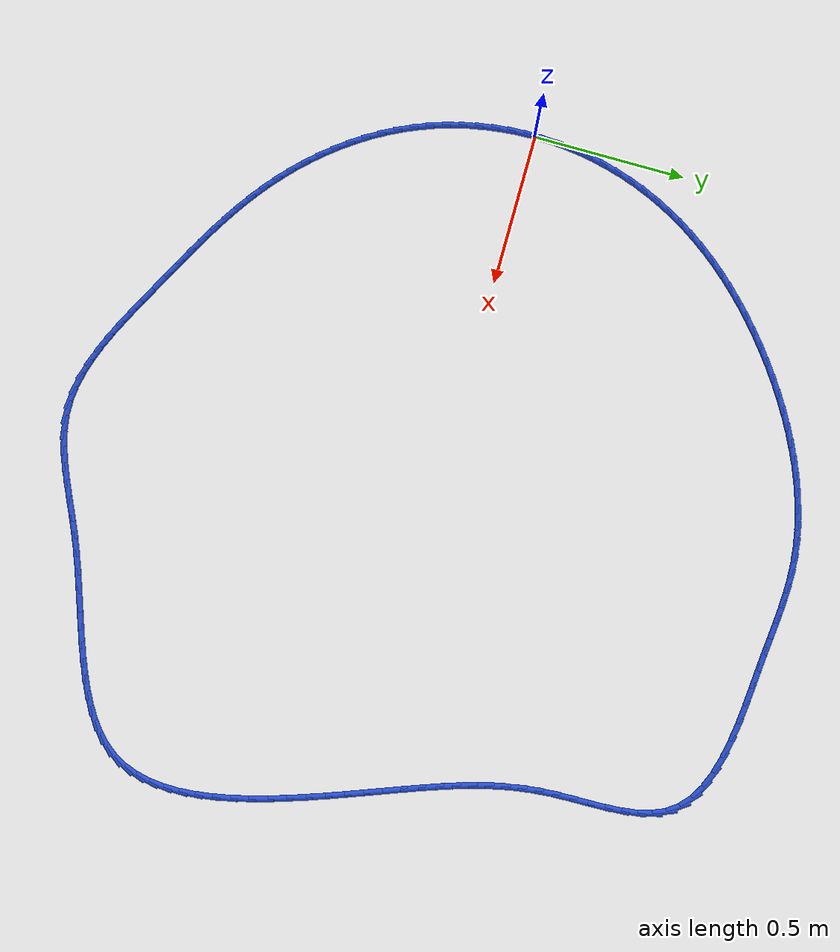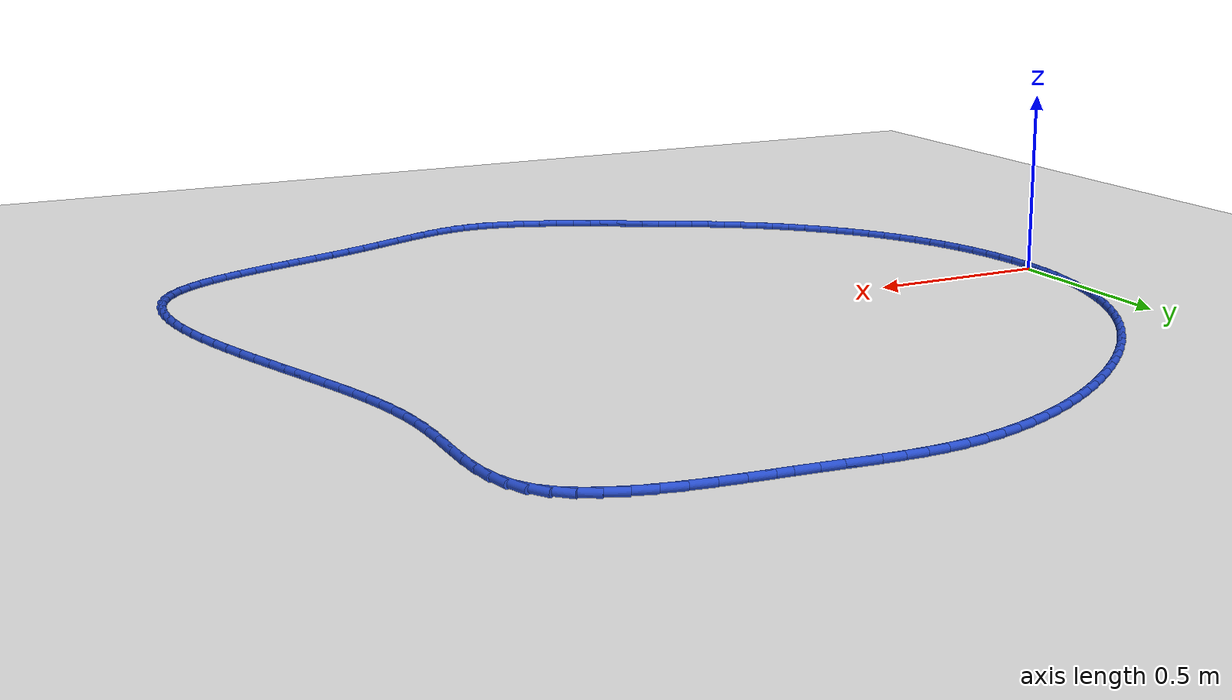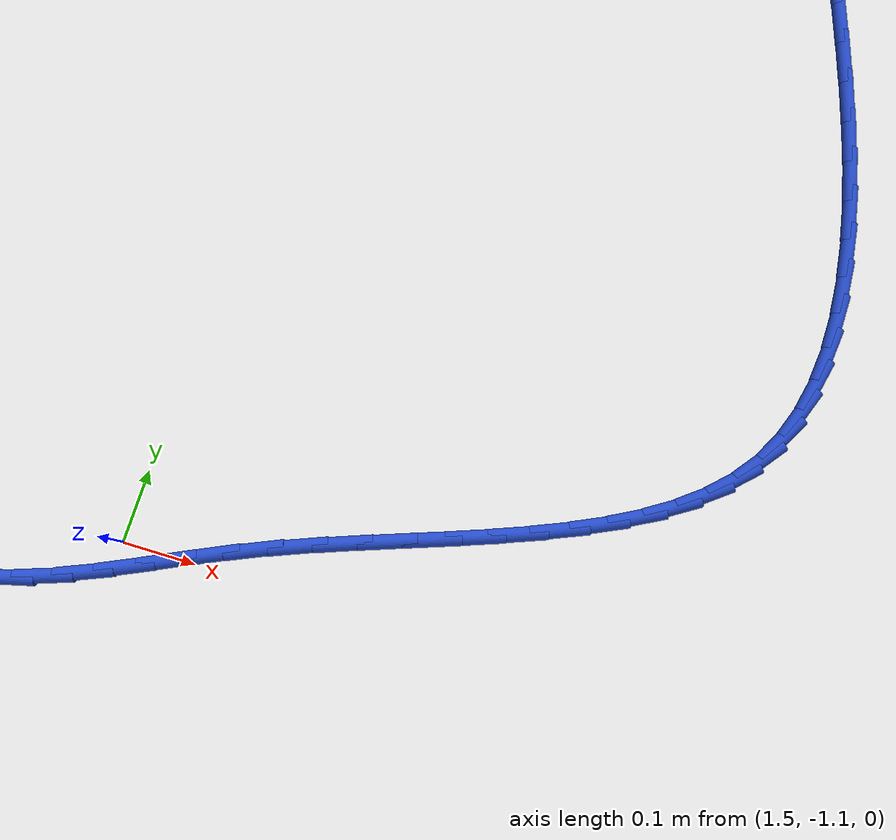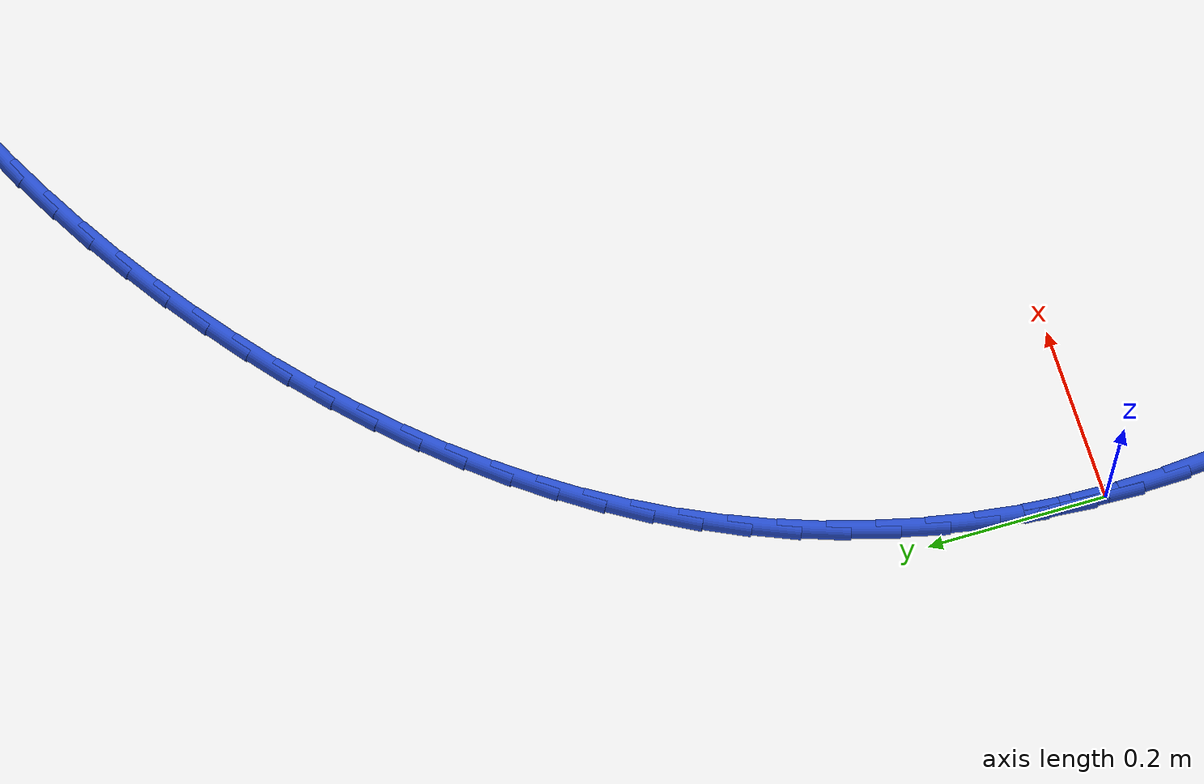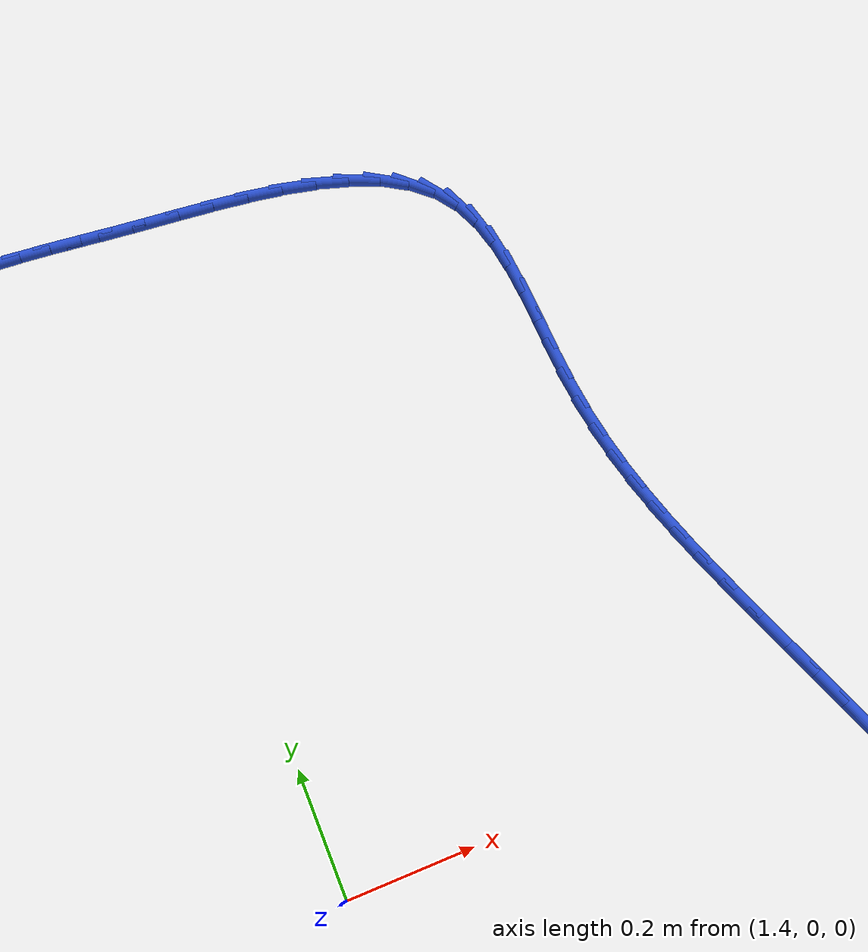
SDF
<sdf version="1.6">
 <world name="default">
  <light name="sun" type="directional">
   <pose>0 0 10 0 -0 0</pose>
   <diffuse>0.8 0.8 0.8 1</diffuse>
   <specular>0.2 0.2 0.2 1</specular>
   <attenuation>
    <range>1000</range>
    <constant>0.9</constant>
    <linear>0.01</linear>
    <quadratic>0.001</quadratic>
   </attenuation>
   <direction>-0.5 0.1 -0.9</direction>
  </light>
  <model name="ground_plane">
   <static>1</static>
   <link name="link">
    <collision name="collision">
     <geometry><plane><normal>0 0 1</normal><size>100 100</size></plane></geometry>
     <surface><friction><ode><mu>100</mu><mu2>50</mu2></ode></friction></surface>
    </collision>
    <visual name="visual">
     <cast_shadows>0</cast_shadows>
     <geometry><plane><normal>0 0 1</normal><size>100 100</size></plane></geometry>
     <material>
      <script><uri>file://media/materials/scripts/gazebo.material</uri><name>Gazebo/WhiteGlow</name></script>
     </material>
    </visual>
   </link>
  </model>
  <gravity>0 0 -9.8</gravity>
  <magnetic_field>6e-06 2.3e-05 -4.2e-05</magnetic_field>
  <atmosphere type="adiabatic"/>
  <physics name="default_physics" default="0" type="ode">
   <max_step_size>0.001</max_step_size>
   <real_time_factor>1</real_time_factor>
   <real_time_update_rate>1000</real_time_update_rate>
  </physics>
  <scene><ambient>0.4 0.4 0.4 1</ambient><background>0.7 0.7 0.7 1</background><shadows>1</shadows></scene>
  <spherical_coordinates>
   <surface_model>EARTH_WGS84</surface_model>
   <latitude_deg>0</latitude_deg>
   <longitude_deg>0</longitude_deg>
   <elevation>0</elevation>
   <heading_deg>0</heading_deg>
  </spherical_coordinates>
  <model name="line">
   <link name="link_0">
    <pose>1.3877787807814457e-17 1.249000902703301e-16 0.01 0 1.57 1.5397155368790938</pose>
    <collision name="collision">
     <geometry><cylinder><radius>0.01</radius><length>0.08</length></cylinder></geometry>
    </collision>
    <visual name="visual">
     <material>
      <script><name>Gazebo/Blue</name><uri>file://media/materials/scripts/gazebo.material</uri></script>
     </material>
     <geometry><cylinder><radius>0.01</radius><length>0.08</length></cylinder></geometry>
    </visual>
   </link>
   <link name="link_1">
    <pose>0.0016496396402193626 0.053058767746443615 0.01 0 1.57 1.486767750287063</pose>
    <collision name="collision">
     <geometry><cylinder><radius>0.01</radius><length>0.08</length></cylinder></geometry>
    </collision>
    <visual name="visual">
     <material>
      <script><name>Gazebo/Blue</name><uri>file://media/materials/scripts/gazebo.material</uri></script>
     </material>
     <geometry><cylinder><radius>0.01</radius><length>0.08</length></cylinder></geometry>
    </visual>
   </link>
   <link name="link_2">
    <pose>0.0061066257631755255 0.10597518501267404 0.01 0 1.57 1.4346172440166665</pose>
    <collision name="collision">
     <geometry><cylinder><radius>0.01</radius><length>0.08</length></cylinder></geometry>
    </collision>
    <visual name="visual">
     <material>
      <script><name>Gazebo/Blue</name><uri>file://media/materials/scripts/gazebo.material</uri></script>
     </material>
     <geometry><cylinder><radius>0.01</radius><length>0.08</length></cylinder></geometry>
    </visual>
   </link>
   <link name="link_3">
    <pose>0.013315982126956843 0.15858778750707223 0.01 0 1.57 1.383057350820544</pose>
    <collision name="collision">
     <geometry><cylinder><radius>0.01</radius><length>0.08</length></cylinder></geometry>
    </collision>
    <visual name="visual">
     <material>
      <script><name>Gazebo/Blue</name><uri>file://media/materials/scripts/gazebo.material</uri></script>
     </material>
     <geometry><cylinder><radius>0.01</radius><length>0.08</length></cylinder></geometry>
    </visual>
   </link>
   <link name="link_4">
    <pose>0.023222732489651655 0.21073511093801858 0.01 0 1.57 1.3318730193041797</pose>
    <collision name="collision">
     <geometry><cylinder><radius>0.01</radius><length>0.08</length></cylinder></geometry>
    </collision>
    <visual name="visual">
     <material>
      <script><name>Gazebo/Blue</name><uri>file://media/materials/scripts/gazebo.material</uri></script>
     </material>
     <geometry><cylinder><radius>0.01</radius><length>0.08</length></cylinder></geometry>
    </visual>
   </link>
   <link name="link_5">
    <pose>0.035771900609348345 0.26225569101389395 0.01 0 1.57 1.2808430059323457</pose>
    <collision name="collision">
     <geometry><cylinder><radius>0.01</radius><length>0.08</length></cylinder></geometry>
    </collision>
    <visual name="visual">
     <material>
      <script><name>Gazebo/Blue</name><uri>file://media/materials/scripts/gazebo.material</uri></script>
     </material>
     <geometry><cylinder><radius>0.01</radius><length>0.08</length></cylinder></geometry>
    </visual>
   </link>
   <link name="link_6">
    <pose>0.05090851024413523 0.312988063443079 0.01 0 1.57 1.22974162803838</pose>
    <collision name="collision">
     <geometry><cylinder><radius>0.01</radius><length>0.08</length></cylinder></geometry>
    </collision>
    <visual name="visual">
     <material>
      <script><name>Gazebo/Blue</name><uri>file://media/materials/scripts/gazebo.material</uri></script>
     </material>
     <geometry><cylinder><radius>0.01</radius><length>0.08</length></cylinder></geometry>
    </visual>
   </link>
   <link name="link_7">
    <pose>0.06857758515210063 0.3627707639339541 0.01 0 1.57 1.1783402987478335</pose>
    <collision name="collision">
     <geometry><cylinder><radius>0.01</radius><length>0.08</length></cylinder></geometry>
    </collision>
    <visual name="visual">
     <material>
      <script><name>Gazebo/Blue</name><uri>file://media/materials/scripts/gazebo.material</uri></script>
     </material>
     <geometry><cylinder><radius>0.01</radius><length>0.08</length></cylinder></geometry>
    </visual>
   </link>
   <link name="link_8">
    <pose>0.08872414909133301 0.41144232819490034 0.01 0 1.57 1.1264639910470764</pose>
    <collision name="collision">
     <geometry><cylinder><radius>0.01</radius><length>0.08</length></cylinder></geometry>
    </collision>
    <visual name="visual">
     <material>
      <script><name>Gazebo/Blue</name><uri>file://media/materials/scripts/gazebo.material</uri></script>
     </material>
     <geometry><cylinder><radius>0.01</radius><length>0.08</length></cylinder></geometry>
    </visual>
   </link>
   <link name="link_9">
    <pose>0.1112921193246824 0.45884567432193646 0.01 0 1.57 1.0750662802315014</pose>
    <collision name="collision">
     <geometry><cylinder><radius>0.01</radius><length>0.08</length></cylinder></geometry>
    </collision>
    <visual name="visual">
     <material>
      <script><name>Gazebo/Blue</name><uri>file://media/materials/scripts/gazebo.material</uri></script>
     </material>
     <geometry><cylinder><radius>0.01</radius><length>0.08</length></cylinder></geometry>
    </visual>
   </link>
   <link name="link_10">
    <pose>0.13620322907181076 0.5049115825846231 0.01 0 1.57 1.02527825872554</pose>
    <collision name="collision">
     <geometry><cylinder><radius>0.01</radius><length>0.08</length></cylinder></geometry>
    </collision>
    <visual name="visual">
     <material>
      <script><name>Gazebo/Blue</name><uri>file://media/materials/scripts/gazebo.material</uri></script>
     </material>
     <geometry><cylinder><radius>0.01</radius><length>0.08</length></cylinder></geometry>
    </visual>
   </link>
   <link name="link_11">
    <pose>0.16335870290310434 0.5496520598569965 0.01 0 1.57 0.9772844430796144</pose>
    <collision name="collision">
     <geometry><cylinder><radius>0.01</radius><length>0.08</length></cylinder></geometry>
    </collision>
    <visual name="visual">
     <material>
      <script><name>Gazebo/Blue</name><uri>file://media/materials/scripts/gazebo.material</uri></script>
     </material>
     <geometry><cylinder><radius>0.01</radius><length>0.08</length></cylinder></geometry>
    </visual>
   </link>
   <link name="link_12">
    <pose>0.19265899462035108 0.5930821657210138 0.01 0 1.57 0.931187896122774</pose>
    <collision name="collision">
     <geometry><cylinder><radius>0.01</radius><length>0.08</length></cylinder></geometry>
    </collision>
    <visual name="visual">
     <material>
      <script><name>Gazebo/Blue</name><uri>file://media/materials/scripts/gazebo.material</uri></script>
     </material>
     <geometry><cylinder><radius>0.01</radius><length>0.08</length></cylinder></geometry>
    </visual>
   </link>
   <link name="link_13">
    <pose>0.22400455802533917 0.6352169597586321 0.01 0 1.57 0.8870516670950145</pose>
    <collision name="collision">
     <geometry><cylinder><radius>0.01</radius><length>0.08</length></cylinder></geometry>
    </collision>
    <visual name="visual">
     <material>
      <script><name>Gazebo/Blue</name><uri>file://media/materials/scripts/gazebo.material</uri></script>
     </material>
     <geometry><cylinder><radius>0.01</radius><length>0.08</length></cylinder></geometry>
    </visual>
   </link>
   <link name="link_14">
    <pose>0.2572958469198563 0.6760715015518078 0.01 0 1.57 0.8449032430488221</pose>
    <collision name="collision">
     <geometry><cylinder><radius>0.01</radius><length>0.08</length></cylinder></geometry>
    </collision>
    <visual name="visual">
     <material>
      <script><name>Gazebo/Blue</name><uri>file://media/materials/scripts/gazebo.material</uri></script>
     </material>
     <geometry><cylinder><radius>0.01</radius><length>0.08</length></cylinder></geometry>
    </visual>
   </link>
   <link name="link_15">
    <pose>0.2924333151056908 0.7156608506824981 0.01 0 1.57 0.8047396836634639</pose>
    <collision name="collision">
     <geometry><cylinder><radius>0.01</radius><length>0.08</length></cylinder></geometry>
    </collision>
    <visual name="visual">
     <material>
      <script><name>Gazebo/Blue</name><uri>file://media/materials/scripts/gazebo.material</uri></script>
     </material>
     <geometry><cylinder><radius>0.01</radius><length>0.08</length></cylinder></geometry>
    </visual>
   </link>
   <link name="link_16">
    <pose>0.3293174163846304 0.7540000667326596 0.01 0 1.57 0.766532954358081</pose>
    <collision name="collision">
     <geometry><cylinder><radius>0.01</radius><length>0.08</length></cylinder></geometry>
    </collision>
    <visual name="visual">
     <material>
      <script><name>Gazebo/Blue</name><uri>file://media/materials/scripts/gazebo.material</uri></script>
     </material>
     <geometry><cylinder><radius>0.01</radius><length>0.08</length></cylinder></geometry>
    </visual>
   </link>
   <link name="link_17">
    <pose>0.3678486045584633 0.7911042092842493 0.01 0 1.57 0.7302350898071815</pose>
    <collision name="collision">
     <geometry><cylinder><radius>0.01</radius><length>0.08</length></cylinder></geometry>
    </collision>
    <visual name="visual">
     <material>
      <script><name>Gazebo/Blue</name><uri>file://media/materials/scripts/gazebo.material</uri></script>
     </material>
     <geometry><cylinder><radius>0.01</radius><length>0.08</length></cylinder></geometry>
    </visual>
   </link>
   <link name="link_18">
    <pose>0.4079273334289774 0.826988337919224 0.01 0 1.57 0.6957829390940024</pose>
    <collision name="collision">
     <geometry><cylinder><radius>0.01</radius><length>0.08</length></cylinder></geometry>
    </collision>
    <visual name="visual">
     <material>
      <script><name>Gazebo/Blue</name><uri>file://media/materials/scripts/gazebo.material</uri></script>
     </material>
     <geometry><cylinder><radius>0.01</radius><length>0.08</length></cylinder></geometry>
    </visual>
   </link>
   <link name="link_19">
    <pose>0.44945405679796085 0.8616675122195406 0.01 0 1.57 0.663051465752296</pose>
    <collision name="collision">
     <geometry><cylinder><radius>0.01</radius><length>0.08</length></cylinder></geometry>
    </collision>
    <visual name="visual">
     <material>
      <script><name>Gazebo/Blue</name><uri>file://media/materials/scripts/gazebo.material</uri></script>
     </material>
     <geometry><cylinder><radius>0.01</radius><length>0.08</length></cylinder></geometry>
    </visual>
   </link>
   <link name="link_20">
    <pose>0.49232901586469335 0.8951531132384675 0.01 0 1.57 0.630773106916503</pose>
    <collision name="collision">
     <geometry><cylinder><radius>0.01</radius><length>0.08</length></cylinder></geometry>
    </collision>
    <visual name="visual">
     <material>
      <script><name>Gazebo/Blue</name><uri>file://media/materials/scripts/gazebo.material</uri></script>
     </material>
     <geometry><cylinder><radius>0.01</radius><length>0.08</length></cylinder></geometry>
    </visual>
   </link>
   <link name="link_21">
    <pose>0.5364476192525597 0.9273729069805606 0.01 0 1.57 0.5975806511527267</pose>
    <collision name="collision">
     <geometry><cylinder><radius>0.01</radius><length>0.08</length></cylinder></geometry>
    </collision>
    <visual name="visual">
     <material>
      <script><name>Gazebo/Blue</name><uri>file://media/materials/scripts/gazebo.material</uri></script>
     </material>
     <geometry><cylinder><radius>0.01</radius><length>0.08</length></cylinder></geometry>
    </visual>
   </link>
   <link name="link_22">
    <pose>0.5817004746196611 0.9581715913403834 0.01 0 1.57 0.5631741896335456</pose>
    <collision name="collision">
     <geometry><cylinder><radius>0.01</radius><length>0.08</length></cylinder></geometry>
    </collision>
    <visual name="visual">
     <material>
      <script><name>Gazebo/Blue</name><uri>file://media/materials/scripts/gazebo.material</uri></script>
     </material>
     <geometry><cylinder><radius>0.01</radius><length>0.08</length></cylinder></geometry>
    </visual>
   </link>
   <link name="link_23">
    <pose>0.6279779833437995 0.9873902950730319 0.01 0 1.57 0.5272971381579243</pose>
    <collision name="collision">
     <geometry><cylinder><radius>0.01</radius><length>0.08</length></cylinder></geometry>
    </collision>
    <visual name="visual">
     <material>
      <script><name>Gazebo/Blue</name><uri>file://media/materials/scripts/gazebo.material</uri></script>
     </material>
     <geometry><cylinder><radius>0.01</radius><length>0.08</length></cylinder></geometry>
    </visual>
   </link>
   <link name="link_24">
    <pose>0.675170546802775 1.0148701469336008 0.01 0 1.57 0.48968454022798497</pose>
    <collision name="collision">
     <geometry><cylinder><radius>0.01</radius><length>0.08</length></cylinder></geometry>
    </collision>
    <visual name="visual">
     <material>
      <script><name>Gazebo/Blue</name><uri>file://media/materials/scripts/gazebo.material</uri></script>
     </material>
     <geometry><cylinder><radius>0.01</radius><length>0.08</length></cylinder></geometry>
    </visual>
   </link>
   <link name="link_25">
    <pose>0.7231685663743896 1.0404522756771863 0.01 0 1.57 0.45006178031251953</pose>
    <collision name="collision">
     <geometry><cylinder><radius>0.01</radius><length>0.08</length></cylinder></geometry>
    </collision>
    <visual name="visual">
     <material>
      <script><name>Gazebo/Blue</name><uri>file://media/materials/scripts/gazebo.material</uri></script>
     </material>
     <geometry><cylinder><radius>0.01</radius><length>0.08</length></cylinder></geometry>
    </visual>
   </link>
   <link name="link_26">
    <pose>0.7718624434364442 1.0639778100588837 0.01 0 1.57 0.4081446542346879</pose>
    <collision name="collision">
     <geometry><cylinder><radius>0.01</radius><length>0.08</length></cylinder></geometry>
    </collision>
    <visual name="visual">
     <material>
      <script><name>Gazebo/Blue</name><uri>file://media/materials/scripts/gazebo.material</uri></script>
     </material>
     <geometry><cylinder><radius>0.01</radius><length>0.08</length></cylinder></geometry>
    </visual>
   </link>
   <link name="link_27">
    <pose>0.8211425793667394 1.0852878788337879 0.01 0 1.57 0.36364127158582243</pose>
    <collision name="collision">
     <geometry><cylinder><radius>0.01</radius><length>0.08</length></cylinder></geometry>
    </collision>
    <visual name="visual">
     <material>
      <script><name>Gazebo/Blue</name><uri>file://media/materials/scripts/gazebo.material</uri></script>
     </material>
     <geometry><cylinder><radius>0.01</radius><length>0.08</length></cylinder></geometry>
    </visual>
   </link>
   <link name="link_28">
    <pose>0.8708993755430775 1.1042236107569954 0.01 0 1.57 0.31625643321056335</pose>
    <collision name="collision">
     <geometry><cylinder><radius>0.01</radius><length>0.08</length></cylinder></geometry>
    </collision>
    <visual name="visual">
     <material>
      <script><name>Gazebo/Blue</name><uri>file://media/materials/scripts/gazebo.material</uri></script>
     </material>
     <geometry><cylinder><radius>0.01</radius><length>0.08</length></cylinder></geometry>
    </visual>
   </link>
   <link name="link_29">
    <pose>0.9210232333432591 1.1206261345836015 0.01 0 1.57 0.2656992879545503</pose>
    <collision name="collision">
     <geometry><cylinder><radius>0.01</radius><length>0.08</length></cylinder></geometry>
    </collision>
    <visual name="visual">
     <material>
      <script><name>Gazebo/Blue</name><uri>file://media/materials/scripts/gazebo.material</uri></script>
     </material>
     <geometry><cylinder><radius>0.01</radius><length>0.08</length></cylinder></geometry>
    </visual>
   </link>
   <link name="link_30">
    <pose>0.9714045541450855 1.1343365790687014 0.01 0 1.57 0.21169518020030623</pose>
    <collision name="collision">
     <geometry><cylinder><radius>0.01</radius><length>0.08</length></cylinder></geometry>
    </collision>
    <visual name="visual">
     <material>
      <script><name>Gazebo/Blue</name><uri>file://media/materials/scripts/gazebo.material</uri></script>
     </material>
     <geometry><cylinder><radius>0.01</radius><length>0.08</length></cylinder></geometry>
    </visual>
   </link>
   <link name="link_31">
    <pose>1.0219337393263574 1.1451960729673907 0.01 0 1.57 0.15400256957993785</pose>
    <collision name="collision">
     <geometry><cylinder><radius>0.01</radius><length>0.08</length></cylinder></geometry>
    </collision>
    <visual name="visual">
     <material>
      <script><name>Gazebo/Blue</name><uri>file://media/materials/scripts/gazebo.material</uri></script>
     </material>
     <geometry><cylinder><radius>0.01</radius><length>0.08</length></cylinder></geometry>
    </visual>
   </link>
   <link name="link_32">
    <pose>1.0725011902648767 1.153045745034765 0.01 0 1.57 0.09243560905928495</pose>
    <collision name="collision">
     <geometry><cylinder><radius>0.01</radius><length>0.08</length></cylinder></geometry>
    </collision>
    <visual name="visual">
     <material>
      <script><name>Gazebo/Blue</name><uri>file://media/materials/scripts/gazebo.material</uri></script>
     </material>
     <geometry><cylinder><radius>0.01</radius><length>0.08</length></cylinder></geometry>
    </visual>
   </link>
   <link name="link_33">
    <pose>1.1229973083384441 1.15772672402592 0.01 0 1.57 0.029247220058521664</pose>
    <collision name="collision">
     <geometry><cylinder><radius>0.01</radius><length>0.08</length></cylinder></geometry>
    </collision>
    <visual name="visual">
     <material>
      <script><name>Gazebo/Blue</name><uri>file://media/materials/scripts/gazebo.material</uri></script>
     </material>
     <geometry><cylinder><radius>0.01</radius><length>0.08</length></cylinder></geometry>
    </visual>
   </link>
   <link name="link_34">
    <pose>1.1733907742856655 1.1592010132068942 0.01 0 1.57 -0.024491602089216087</pose>
    <collision name="collision">
     <geometry><cylinder><radius>0.01</radius><length>0.08</length></cylinder></geometry>
    </collision>
    <visual name="visual">
     <material>
      <script><name>Gazebo/Blue</name><uri>file://media/materials/scripts/gazebo.material</uri></script>
     </material>
     <geometry><cylinder><radius>0.01</radius><length>0.08</length></cylinder></geometry>
    </visual>
   </link>
   <link name="link_35">
    <pose>1.2239940162210248 1.1579614108773129 0.01 0 1.57 -0.0646316995367665</pose>
    <collision name="collision">
     <geometry><cylinder><radius>0.01</radius><length>0.08</length></cylinder></geometry>
    </collision>
    <visual name="visual">
     <material>
      <script><name>Gazebo/Blue</name><uri>file://media/materials/scripts/gazebo.material</uri></script>
     </material>
     <geometry><cylinder><radius>0.01</radius><length>0.08</length></cylinder></geometry>
    </visual>
   </link>
   <link name="link_36">
    <pose>1.2752137911200274 1.1546463725678595 0.01 0 1.57 -0.09071010067974519</pose>
    <collision name="collision">
     <geometry><cylinder><radius>0.01</radius><length>0.08</length></cylinder></geometry>
    </collision>
    <visual name="visual">
     <material>
      <script><name>Gazebo/Blue</name><uri>file://media/materials/scripts/gazebo.material</uri></script>
     </material>
     <geometry><cylinder><radius>0.01</radius><length>0.08</length></cylinder></geometry>
    </visual>
   </link>
   <link name="link_37">
    <pose>1.3274568585449105 1.1498943578034995 0.01 0 1.57 -0.10304732148852294</pose>
    <collision name="collision">
     <geometry><cylinder><radius>0.01</radius><length>0.08</length></cylinder></geometry>
    </collision>
    <visual name="visual">
     <material>
      <script><name>Gazebo/Blue</name><uri>file://media/materials/scripts/gazebo.material</uri></script>
     </material>
     <geometry><cylinder><radius>0.01</radius><length>0.08</length></cylinder></geometry>
    </visual>
   </link>
   <link name="link_38">
    <pose>1.3811299780579092 1.1443438261091976 0.01 0 1.57 -0.10251445731559321</pose>
    <collision name="collision">
     <geometry><cylinder><radius>0.01</radius><length>0.08</length></cylinder></geometry>
    </collision>
    <visual name="visual">
     <material>
      <script><name>Gazebo/Blue</name><uri>file://media/materials/scripts/gazebo.material</uri></script>
     </material>
     <geometry><cylinder><radius>0.01</radius><length>0.08</length></cylinder></geometry>
    </visual>
   </link>
   <link name="link_39">
    <pose>1.43663990922126 1.138633237009918 0.01 0 1.57 -0.09242456907437945</pose>
    <collision name="collision">
     <geometry><cylinder><radius>0.01</radius><length>0.08</length></cylinder></geometry>
    </collision>
    <visual name="visual">
     <material>
      <script><name>Gazebo/Blue</name><uri>file://media/materials/scripts/gazebo.material</uri></script>
     </material>
     <geometry><cylinder><radius>0.01</radius><length>0.08</length></cylinder></geometry>
    </visual>
   </link>
   <link name="link_40">
    <pose>1.4942756534083494 1.1332910580200908 0.01 0 1.57 -0.08934370611154342</pose>
    <collision name="collision">
     <geometry><cylinder><radius>0.01</radius><length>0.08</length></cylinder></geometry>
    </collision>
    <visual name="visual">
     <material>
      <script><name>Gazebo/Blue</name><uri>file://media/materials/scripts/gazebo.material</uri></script>
     </material>
     <geometry><cylinder><radius>0.01</radius><length>0.08</length></cylinder></geometry>
    </visual>
   </link>
   <link name="link_41">
    <pose>1.553413619160161 1.1279933495186643 0.01 0 1.57 -0.09993796721931673</pose>
    <collision name="collision">
     <geometry><cylinder><radius>0.01</radius><length>0.08</length></cylinder></geometry>
    </collision>
    <visual name="visual">
     <material>
      <script><name>Gazebo/Blue</name><uri>file://media/materials/scripts/gazebo.material</uri></script>
     </material>
     <geometry><cylinder><radius>0.01</radius><length>0.08</length></cylinder></geometry>
    </visual>
   </link>
   <link name="link_42">
    <pose>1.61300403490625 1.1220180984447343 0.01 0 1.57 -0.12440871492177794</pose>
    <collision name="collision">
     <geometry><cylinder><radius>0.01</radius><length>0.08</length></cylinder></geometry>
    </collision>
    <visual name="visual">
     <material>
      <script><name>Gazebo/Blue</name><uri>file://media/materials/scripts/gazebo.material</uri></script>
     </material>
     <geometry><cylinder><radius>0.01</radius><length>0.08</length></cylinder></geometry>
    </visual>
   </link>
   <link name="link_43">
    <pose>1.6719947225764202 1.114641043946829 0.01 0 1.57 -0.1642433411252326</pose>
    <collision name="collision">
     <geometry><cylinder><radius>0.01</radius><length>0.08</length></cylinder></geometry>
    </collision>
    <visual name="visual">
     <material>
      <script><name>Gazebo/Blue</name><uri>file://media/materials/scripts/gazebo.material</uri></script>
     </material>
     <geometry><cylinder><radius>0.01</radius><length>0.08</length></cylinder></geometry>
    </visual>
   </link>
   <link name="link_44">
    <pose>1.729333504100478 1.1051379251734785 0.01 0 1.57 -0.22237057410697364</pose>
    <collision name="collision">
     <geometry><cylinder><radius>0.01</radius><length>0.08</length></cylinder></geometry>
    </collision>
    <visual name="visual">
     <material>
      <script><name>Gazebo/Blue</name><uri>file://media/materials/scripts/gazebo.material</uri></script>
     </material>
     <geometry><cylinder><radius>0.01</radius><length>0.08</length></cylinder></geometry>
    </visual>
   </link>
   <link name="link_45">
    <pose>1.7839682014082259 1.0927844812732115 0.01 0 1.57 -0.3033954484459668</pose>
    <collision name="collision">
     <geometry><cylinder><radius>0.01</radius><length>0.08</length></cylinder></geometry>
    </collision>
    <visual name="visual">
     <material>
      <script><name>Gazebo/Blue</name><uri>file://media/materials/scripts/gazebo.material</uri></script>
     </material>
     <geometry><cylinder><radius>0.01</radius><length>0.08</length></cylinder></geometry>
    </visual>
   </link>
   <link name="link_46">
    <pose>1.8348466364294709 1.0768564513945582 0.01 0 1.57 -0.4137078737110211</pose>
    <collision name="collision">
     <geometry><cylinder><radius>0.01</radius><length>0.08</length></cylinder></geometry>
    </collision>
    <visual name="visual">
     <material>
      <script><name>Gazebo/Blue</name><uri>file://media/materials/scripts/gazebo.material</uri></script>
     </material>
     <geometry><cylinder><radius>0.01</radius><length>0.08</length></cylinder></geometry>
    </visual>
   </link>
   <link name="link_47">
    <pose>1.8809166310940164 1.056629574686048 0.01 0 1.57 -0.560726887230613</pose>
    <collision name="collision">
     <geometry><cylinder><radius>0.01</radius><length>0.08</length></cylinder></geometry>
    </collision>
    <visual name="visual">
     <material>
      <script><name>Gazebo/Blue</name><uri>file://media/materials/scripts/gazebo.material</uri></script>
     </material>
     <geometry><cylinder><radius>0.01</radius><length>0.08</length></cylinder></geometry>
    </visual>
   </link>
   <link name="link_48">
    <pose>1.9211260073316685 1.03137959029621 0.01 0 1.57 -0.7496522175061833</pose>
    <collision name="collision">
     <geometry><cylinder><radius>0.01</radius><length>0.08</length></cylinder></geometry>
    </collision>
    <visual name="visual">
     <material>
      <script><name>Gazebo/Blue</name><uri>file://media/materials/scripts/gazebo.material</uri></script>
     </material>
     <geometry><cylinder><radius>0.01</radius><length>0.08</length></cylinder></geometry>
    </visual>
   </link>
   <link name="link_49">
    <pose>1.954422587072231 1.0003822373735738 0.01 0 1.57 -0.9754536804189096</pose>
    <collision name="collision">
     <geometry><cylinder><radius>0.01</radius><length>0.08</length></cylinder></geometry>
    </collision>
    <visual name="visual">
     <material>
      <script><name>Gazebo/Blue</name><uri>file://media/materials/scripts/gazebo.material</uri></script>
     </material>
     <geometry><cylinder><radius>0.01</radius><length>0.08</length></cylinder></geometry>
    </visual>
   </link>
   <link name="link_50">
    <pose>1.9797851643200544 0.9629368210913767 0.01 0 1.57 -1.190105979229469</pose>
    <collision name="collision">
     <geometry><cylinder><radius>0.01</radius><length>0.08</length></cylinder></geometry>
    </collision>
    <visual name="visual">
     <material>
      <script><name>Gazebo/Blue</name><uri>file://media/materials/scripts/gazebo.material</uri></script>
     </material>
     <geometry><cylinder><radius>0.01</radius><length>0.08</length></cylinder></geometry>
    </visual>
   </link>
   <link name="link_51">
    <pose>1.9972962529762357 0.9191824447551955 0.01 0 1.57 -1.3470797712673916</pose>
    <collision name="collision">
     <geometry><cylinder><radius>0.01</radius><length>0.08</length></cylinder></geometry>
    </collision>
    <visual name="visual">
     <material>
      <script><name>Gazebo/Blue</name><uri>file://media/materials/scripts/gazebo.material</uri></script>
     </material>
     <geometry><cylinder><radius>0.01</radius><length>0.08</length></cylinder></geometry>
    </visual>
   </link>
   <link name="link_52">
    <pose>2.0084166596154334 0.8703069266720129 0.01 0 1.57 -1.4523370505065756</pose>
    <collision name="collision">
     <geometry><cylinder><radius>0.01</radius><length>0.08</length></cylinder></geometry>
    </collision>
    <visual name="visual">
     <material>
      <script><name>Gazebo/Blue</name><uri>file://media/materials/scripts/gazebo.material</uri></script>
     </material>
     <geometry><cylinder><radius>0.01</radius><length>0.08</length></cylinder></geometry>
    </visual>
   </link>
   <link name="link_53">
    <pose>2.014693928456514 0.8175640820668949 0.01 0 1.57 -1.5169850400806506</pose>
    <collision name="collision">
     <geometry><cylinder><radius>0.01</radius><length>0.08</length></cylinder></geometry>
    </collision>
    <visual name="visual">
     <material>
      <script><name>Gazebo/Blue</name><uri>file://media/materials/scripts/gazebo.material</uri></script>
     </material>
     <geometry><cylinder><radius>0.01</radius><length>0.08</length></cylinder></geometry>
    </visual>
   </link>
   <link name="link_54">
    <pose>2.0176756037183456 0.7622077261649062 0.01 0 1.57 -1.5490488431457825</pose>
    <collision name="collision">
     <geometry><cylinder><radius>0.01</radius><length>0.08</length></cylinder></geometry>
    </collision>
    <visual name="visual">
     <material>
      <script><name>Gazebo/Blue</name><uri>file://media/materials/scripts/gazebo.material</uri></script>
     </material>
     <geometry><cylinder><radius>0.01</radius><length>0.08</length></cylinder></geometry>
    </visual>
   </link>
   <link name="link_55">
    <pose>2.018909229619796 0.7054916741911118 0.01 0 1.57 -1.5526166048127041</pose>
    <collision name="collision">
     <geometry><cylinder><radius>0.01</radius><length>0.08</length></cylinder></geometry>
    </collision>
    <visual name="visual">
     <material>
      <script><name>Gazebo/Blue</name><uri>file://media/materials/scripts/gazebo.material</uri></script>
     </material>
     <geometry><cylinder><radius>0.01</radius><length>0.08</length></cylinder></geometry>
    </visual>
   </link>
   <link name="link_56">
    <pose>2.0199423503797314 0.6486697413705778 0.01 0 1.57 -1.5280733959697104</pose>
    <collision name="collision">
     <geometry><cylinder><radius>0.01</radius><length>0.08</length></cylinder></geometry>
    </collision>
    <visual name="visual">
     <material>
      <script><name>Gazebo/Blue</name><uri>file://media/materials/scripts/gazebo.material</uri></script>
     </material>
     <geometry><cylinder><radius>0.01</radius><length>0.08</length></cylinder></geometry>
    </visual>
   </link>
   <link name="link_57">
    <pose>2.0223223614791395 0.5929955907504827 0.01 0 1.57 -1.479523611997774</pose>
    <collision name="collision">
     <geometry><cylinder><radius>0.01</radius><length>0.08</length></cylinder></geometry>
    </collision>
    <visual name="visual">
     <material>
      <script><name>Gazebo/Blue</name><uri>file://media/materials/scripts/gazebo.material</uri></script>
     </material>
     <geometry><cylinder><radius>0.01</radius><length>0.08</length></cylinder></geometry>
    </visual>
   </link>
   <link name="link_58">
    <pose>2.027232366978467 0.5393501686363963 0.01 0 1.57 -1.427771837746549</pose>
    <collision name="collision">
     <geometry><cylinder><radius>0.01</radius><length>0.08</length></cylinder></geometry>
    </collision>
    <visual name="visual">
     <material>
      <script><name>Gazebo/Blue</name><uri>file://media/materials/scripts/gazebo.material</uri></script>
     </material>
     <geometry><cylinder><radius>0.01</radius><length>0.08</length></cylinder></geometry>
    </visual>
   </link>
   <link name="link_59">
    <pose>2.0347078042561644 0.4874402114512244 0.01 0 1.57 -1.3788843363374608</pose>
    <collision name="collision">
     <geometry><cylinder><radius>0.01</radius><length>0.08</length></cylinder></geometry>
    </collision>
    <visual name="visual">
     <material>
      <script><name>Gazebo/Blue</name><uri>file://media/materials/scripts/gazebo.material</uri></script>
     </material>
     <geometry><cylinder><radius>0.01</radius><length>0.08</length></cylinder></geometry>
    </visual>
   </link>
   <link name="link_60">
    <pose>2.044558671358158 0.4367418023312113 0.01 0 1.57 -1.3346141325961087</pose>
    <collision name="collision">
     <geometry><cylinder><radius>0.01</radius><length>0.08</length></cylinder></geometry>
    </collision>
    <visual name="visual">
     <material>
      <script><name>Gazebo/Blue</name><uri>file://media/materials/scripts/gazebo.material</uri></script>
     </material>
     <geometry><cylinder><radius>0.01</radius><length>0.08</length></cylinder></geometry>
    </visual>
   </link>
   <link name="link_61">
    <pose>2.0565949663303695 0.38673102441259954 0.01 0 1.57 -1.2964014456067248</pose>
    <collision name="collision">
     <geometry><cylinder><radius>0.01</radius><length>0.08</length></cylinder></geometry>
    </collision>
    <visual name="visual">
     <material>
      <script><name>Gazebo/Blue</name><uri>file://media/materials/scripts/gazebo.material</uri></script>
     </material>
     <geometry><cylinder><radius>0.01</radius><length>0.08</length></cylinder></geometry>
    </visual>
   </link>
   <link name="link_62">
    <pose>2.0706266872187244 0.33688396083163424 0.01 0 1.57 -1.2652395307549769</pose>
    <collision name="collision">
     <geometry><cylinder><radius>0.01</radius><length>0.08</length></cylinder></geometry>
    </collision>
    <visual name="visual">
     <material>
      <script><name>Gazebo/Blue</name><uri>file://media/materials/scripts/gazebo.material</uri></script>
     </material>
     <geometry><cylinder><radius>0.01</radius><length>0.08</length></cylinder></geometry>
    </visual>
   </link>
   <link name="link_63">
    <pose>2.086463832069146 0.2866766947245578 0.01 0 1.57 -1.2416287035753943</pose>
    <collision name="collision">
     <geometry><cylinder><radius>0.01</radius><length>0.08</length></cylinder></geometry>
    </collision>
    <visual name="visual">
     <material>
      <script><name>Gazebo/Blue</name><uri>file://media/materials/scripts/gazebo.material</uri></script>
     </material>
     <geometry><cylinder><radius>0.01</radius><length>0.08</length></cylinder></geometry>
    </visual>
   </link>
   <link name="link_64">
    <pose>2.1039163989275584 0.23558530922761478 0.01 0 1.57 -1.2255698182125174</pose>
    <collision name="collision">
     <geometry><cylinder><radius>0.01</radius><length>0.08</length></cylinder></geometry>
    </collision>
    <visual name="visual">
     <material>
      <script><name>Gazebo/Blue</name><uri>file://media/materials/scripts/gazebo.material</uri></script>
     </material>
     <geometry><cylinder><radius>0.01</radius><length>0.08</length></cylinder></geometry>
    </visual>
   </link>
   <link name="link_65">
    <pose>2.1227890909803784 0.18310698430636518 0.01 0 1.57 -1.215939789729463</pose>
    <collision name="collision">
     <geometry><cylinder><radius>0.01</radius><length>0.08</length></cylinder></geometry>
    </collision>
    <visual name="visual">
     <material>
      <script><name>Gazebo/Blue</name><uri>file://media/materials/scripts/gazebo.material</uri></script>
     </material>
     <geometry><cylinder><radius>0.01</radius><length>0.08</length></cylinder></geometry>
    </visual>
   </link>
   <link name="link_66">
    <pose>2.142785566935916 0.12914150137501645 0.01 0 1.57 -1.2114472267352108</pose>
    <collision name="collision">
     <geometry><cylinder><radius>0.01</radius><length>0.08</length></cylinder></geometry>
    </collision>
    <visual name="visual">
     <material>
      <script><name>Gazebo/Blue</name><uri>file://media/materials/scripts/gazebo.material</uri></script>
     </material>
     <geometry><cylinder><radius>0.01</radius><length>0.08</length></cylinder></geometry>
    </visual>
   </link>
   <link name="link_67">
    <pose>2.1635187732767975 0.07395007548723463 0.01 0 1.57 -1.2116210061415396</pose>
    <collision name="collision">
     <geometry><cylinder><radius>0.01</radius><length>0.08</length></cylinder></geometry>
    </collision>
    <visual name="visual">
     <material>
      <script><name>Gazebo/Blue</name><uri>file://media/materials/scripts/gazebo.material</uri></script>
     </material>
     <geometry><cylinder><radius>0.01</radius><length>0.08</length></cylinder></geometry>
    </visual>
   </link>
   <link name="link_68">
    <pose>2.184598435617007 0.017806754920304663 0.01 0 1.57 -1.2162304734395963</pose>
    <collision name="collision">
     <geometry><cylinder><radius>0.01</radius><length>0.08</length></cylinder></geometry>
    </collision>
    <visual name="visual">
     <material>
      <script><name>Gazebo/Blue</name><uri>file://media/materials/scripts/gazebo.material</uri></script>
     </material>
     <geometry><cylinder><radius>0.01</radius><length>0.08</length></cylinder></geometry>
    </visual>
   </link>
   <link name="link_69">
    <pose>2.2056342795705226 -0.03901441204848701 0.01 0 1.57 -1.2252289311089013</pose>
    <collision name="collision">
     <geometry><cylinder><radius>0.01</radius><length>0.08</length></cylinder></geometry>
    </collision>
    <visual name="visual">
     <material>
      <script><name>Gazebo/Blue</name><uri>file://media/materials/scripts/gazebo.material</uri></script>
     </material>
     <geometry><cylinder><radius>0.01</radius><length>0.08</length></cylinder></geometry>
    </visual>
   </link>
   <link name="link_70">
    <pose>2.2262360307513274 -0.09623937714185546 0.01 0 1.57 -1.2387384780958342</pose>
    <collision name="collision">
     <geometry><cylinder><radius>0.01</radius><length>0.08</length></cylinder></geometry>
    </collision>
    <visual name="visual">
     <material>
      <script><name>Gazebo/Blue</name><uri>file://media/materials/scripts/gazebo.material</uri></script>
     </material>
     <geometry><cylinder><radius>0.01</radius><length>0.08</length></cylinder></geometry>
    </visual>
   </link>
   <link name="link_71">
    <pose>2.2460134147734023 -0.1535940920825142 0.01 0 1.57 -1.2570489514854983</pose>
    <collision name="collision">
     <geometry><cylinder><radius>0.01</radius><length>0.08</length></cylinder></geometry>
    </collision>
    <visual name="visual">
     <material>
      <script><name>Gazebo/Blue</name><uri>file://media/materials/scripts/gazebo.material</uri></script>
     </material>
     <geometry><cylinder><radius>0.01</radius><length>0.08</length></cylinder></geometry>
    </visual>
   </link>
   <link name="link_72">
    <pose>2.2645761572507275 -0.21080450859317787 0.01 0 1.57 -1.2806290459082628</pose>
    <collision name="collision">
     <geometry><cylinder><radius>0.01</radius><length>0.08</length></cylinder></geometry>
    </collision>
    <visual name="visual">
     <material>
      <script><name>Gazebo/Blue</name><uri>file://media/materials/scripts/gazebo.material</uri></script>
     </material>
     <geometry><cylinder><radius>0.01</radius><length>0.08</length></cylinder></geometry>
    </visual>
   </link>
   <link name="link_73">
    <pose>2.2815339837972854 -0.2675965783965617 0.01 0 1.57 -1.3101486203888764</pose>
    <collision name="collision">
     <geometry><cylinder><radius>0.01</radius><length>0.08</length></cylinder></geometry>
    </collision>
    <visual name="visual">
     <material>
      <script><name>Gazebo/Blue</name><uri>file://media/materials/scripts/gazebo.material</uri></script>
     </material>
     <geometry><cylinder><radius>0.01</radius><length>0.08</length></cylinder></geometry>
    </visual>
   </link>
   <link name="link_74">
    <pose>2.296496620027056 -0.3236962532153782 0.01 0 1.57 -1.3465111334952728</pose>
    <collision name="collision">
     <geometry><cylinder><radius>0.01</radius><length>0.08</length></cylinder></geometry>
    </collision>
    <visual name="visual">
     <material>
      <script><name>Gazebo/Blue</name><uri>file://media/materials/scripts/gazebo.material</uri></script>
     </material>
     <geometry><cylinder><radius>0.01</radius><length>0.08</length></cylinder></geometry>
    </visual>
   </link>
   <link name="link_75">
    <pose>2.309073791554022 -0.3788294847723427 0.01 0 1.57 -1.390893389303924</pose>
    <collision name="collision">
     <geometry><cylinder><radius>0.01</radius><length>0.08</length></cylinder></geometry>
    </collision>
    <visual name="visual">
     <material>
      <script><name>Gazebo/Blue</name><uri>file://media/materials/scripts/gazebo.material</uri></script>
     </material>
     <geometry><cylinder><radius>0.01</radius><length>0.08</length></cylinder></geometry>
    </visual>
   </link>
   <link name="link_76">
    <pose>2.3188752239921633 -0.43272222479016925 0.01 0 1.57 -1.4447847303375987</pose>
    <collision name="collision">
     <geometry><cylinder><radius>0.01</radius><length>0.08</length></cylinder></geometry>
    </collision>
    <visual name="visual">
     <material>
      <script><name>Gazebo/Blue</name><uri>file://media/materials/scripts/gazebo.material</uri></script>
     </material>
     <geometry><cylinder><radius>0.01</radius><length>0.08</length></cylinder></geometry>
    </visual>
   </link>
   <link name="link_77">
    <pose>2.3255106429554613 -0.48510042499157235 0.01 0 1.57 -1.5100064303308782</pose>
    <collision name="collision">
     <geometry><cylinder><radius>0.01</radius><length>0.08</length></cylinder></geometry>
    </collision>
    <visual name="visual">
     <material>
      <script><name>Gazebo/Blue</name><uri>file://media/materials/scripts/gazebo.material</uri></script>
     </material>
     <geometry><cylinder><radius>0.01</radius><length>0.08</length></cylinder></geometry>
    </visual>
   </link>
   <link name="link_78">
    <pose>2.328589774057898 -0.535690037099267 0.01 0 1.57 1.5529229942698222</pose>
    <collision name="collision">
     <geometry><cylinder><radius>0.01</radius><length>0.08</length></cylinder></geometry>
    </collision>
    <visual name="visual">
     <material>
      <script><name>Gazebo/Blue</name><uri>file://media/materials/scripts/gazebo.material</uri></script>
     </material>
     <geometry><cylinder><radius>0.01</radius><length>0.08</length></cylinder></geometry>
    </visual>
   </link>
   <link name="link_79">
    <pose>2.3277223429134533 -0.584217012835966 0.01 0 1.57 1.458599328019771</pose>
    <collision name="collision">
     <geometry><cylinder><radius>0.01</radius><length>0.08</length></cylinder></geometry>
    </collision>
    <visual name="visual">
     <material>
      <script><name>Gazebo/Blue</name><uri>file://media/materials/scripts/gazebo.material</uri></script>
     </material>
     <geometry><cylinder><radius>0.01</radius><length>0.08</length></cylinder></geometry>
    </visual>
   </link>
   <link name="link_80">
    <pose>2.3225180751361094 -0.6304073039243845 0.01 0 1.57 1.346732123095638</pose>
    <collision name="collision">
     <geometry><cylinder><radius>0.01</radius><length>0.08</length></cylinder></geometry>
    </collision>
    <visual name="visual">
     <material>
      <script><name>Gazebo/Blue</name><uri>file://media/materials/scripts/gazebo.material</uri></script>
     </material>
     <geometry><cylinder><radius>0.01</radius><length>0.08</length></cylinder></geometry>
    </visual>
   </link>
   <link name="link_81">
    <pose>2.3125866963398467 -0.6739868620872365 0.01 0 1.57 1.2165958881692642</pose>
    <collision name="collision">
     <geometry><cylinder><radius>0.01</radius><length>0.08</length></cylinder></geometry>
    </collision>
    <visual name="visual">
     <material>
      <script><name>Gazebo/Blue</name><uri>file://media/materials/scripts/gazebo.material</uri></script>
     </material>
     <geometry><cylinder><radius>0.01</radius><length>0.08</length></cylinder></geometry>
    </visual>
   </link>
   <link name="link_82">
    <pose>2.2975379321386478 -0.7146816390472374 0.01 0 1.57 1.069761949665185</pose>
    <collision name="collision">
     <geometry><cylinder><radius>0.01</radius><length>0.08</length></cylinder></geometry>
    </collision>
    <visual name="visual">
     <material>
      <script><name>Gazebo/Blue</name><uri>file://media/materials/scripts/gazebo.material</uri></script>
     </material>
     <geometry><cylinder><radius>0.01</radius><length>0.08</length></cylinder></geometry>
    </visual>
   </link>
   <link name="link_83">
    <pose>2.2769815081464917 -0.7522175865270997 0.01 0 1.57 0.9136133449423521</pose>
    <collision name="collision">
     <geometry><cylinder><radius>0.01</radius><length>0.08</length></cylinder></geometry>
    </collision>
    <visual name="visual">
     <material>
      <script><name>Gazebo/Blue</name><uri>file://media/materials/scripts/gazebo.material</uri></script>
     </material>
     <geometry><cylinder><radius>0.01</radius><length>0.08</length></cylinder></geometry>
    </visual>
   </link>
   <link name="link_84">
    <pose>2.2506192923932784 -0.7863831956056533 0.01 0 1.57 0.7719826336899985</pose>
    <collision name="collision">
     <geometry><cylinder><radius>0.01</radius><length>0.08</length></cylinder></geometry>
    </collision>
    <visual name="visual">
     <material>
      <script><name>Gazebo/Blue</name><uri>file://media/materials/scripts/gazebo.material</uri></script>
     </material>
     <geometry><cylinder><radius>0.01</radius><length>0.08</length></cylinder></geometry>
    </visual>
   </link>
   <link name="link_85">
    <pose>2.218772162771013 -0.8173870947959302 0.01 0 1.57 0.6548370400430105</pose>
    <collision name="collision">
     <geometry><cylinder><radius>0.01</radius><length>0.08</length></cylinder></geometry>
    </collision>
    <visual name="visual">
     <material>
      <script><name>Gazebo/Blue</name><uri>file://media/materials/scripts/gazebo.material</uri></script>
     </material>
     <geometry><cylinder><radius>0.01</radius><length>0.08</length></cylinder></geometry>
    </visual>
   </link>
   <link name="link_86">
    <pose>2.1820159156663648 -0.8456109321520637 0.01 0 1.57 0.5611412540439787</pose>
    <collision name="collision">
     <geometry><cylinder><radius>0.01</radius><length>0.08</length></cylinder></geometry>
    </collision>
    <visual name="visual">
     <material>
      <script><name>Gazebo/Blue</name><uri>file://media/materials/scripts/gazebo.material</uri></script>
     </material>
     <geometry><cylinder><radius>0.01</radius><length>0.08</length></cylinder></geometry>
    </visual>
   </link>
   <link name="link_87">
    <pose>2.140927139059118 -0.8714368930021816 0.01 0 1.57 0.48809937263132497</pose>
    <collision name="collision">
     <geometry><cylinder><radius>0.01</radius><length>0.08</length></cylinder></geometry>
    </collision>
    <visual name="visual">
     <material>
      <script><name>Gazebo/Blue</name><uri>file://media/materials/scripts/gazebo.material</uri></script>
     </material>
     <geometry><cylinder><radius>0.01</radius><length>0.08</length></cylinder></geometry>
    </visual>
   </link>
   <link name="link_88">
    <pose>2.096082420929059 -0.8952471626744094 0.01 0 1.57 0.43261044921629677</pose>
    <collision name="collision">
     <geometry><cylinder><radius>0.01</radius><length>0.08</length></cylinder></geometry>
    </collision>
    <visual name="visual">
     <material>
      <script><name>Gazebo/Blue</name><uri>file://media/materials/scripts/gazebo.material</uri></script>
     </material>
     <geometry><cylinder><radius>0.01</radius><length>0.08</length></cylinder></geometry>
    </visual>
   </link>
   <link name="link_89">
    <pose>2.0480583492559723 -0.9174239264968744 0.01 0 1.57 0.3919421929548874</pose>
    <collision name="collision">
     <geometry><cylinder><radius>0.01</radius><length>0.08</length></cylinder></geometry>
    </collision>
    <visual name="visual">
     <material>
      <script><name>Gazebo/Blue</name><uri>file://media/materials/scripts/gazebo.material</uri></script>
     </material>
     <geometry><cylinder><radius>0.01</radius><length>0.08</length></cylinder></geometry>
    </visual>
   </link>
   <link name="link_90">
    <pose>1.9974315120196426 -0.9383493697977039 0.01 0 1.57 0.36394606320995</pose>
    <collision name="collision">
     <geometry><cylinder><radius>0.01</radius><length>0.08</length></cylinder></geometry>
    </collision>
    <visual name="visual">
     <material>
      <script><name>Gazebo/Blue</name><uri>file://media/materials/scripts/gazebo.material</uri></script>
     </material>
     <geometry><cylinder><radius>0.01</radius><length>0.08</length></cylinder></geometry>
    </visual>
   </link>
   <link name="link_91">
    <pose>1.9447784971998547 -0.9584056779050248 0.01 0 1.57 0.3470670155249454</pose>
    <collision name="collision">
     <geometry><cylinder><radius>0.01</radius><length>0.08</length></cylinder></geometry>
    </collision>
    <visual name="visual">
     <material>
      <script><name>Gazebo/Blue</name><uri>file://media/materials/scripts/gazebo.material</uri></script>
     </material>
     <geometry><cylinder><radius>0.01</radius><length>0.08</length></cylinder></geometry>
    </visual>
   </link>
   <link name="link_92">
    <pose>1.890675892776394 -0.9779750361469635 0.01 0 1.57 0.34028603590012435</pose>
    <collision name="collision">
     <geometry><cylinder><radius>0.01</radius><length>0.08</length></cylinder></geometry>
    </collision>
    <visual name="visual">
     <material>
      <script><name>Gazebo/Blue</name><uri>file://media/materials/scripts/gazebo.material</uri></script>
     </material>
     <geometry><cylinder><radius>0.01</radius><length>0.08</length></cylinder></geometry>
    </visual>
   </link>
   <link name="link_93">
    <pose>1.8357002867290464 -0.9974396298516471 0.01 0 1.57 0.34305615118230526</pose>
    <collision name="collision">
     <geometry><cylinder><radius>0.01</radius><length>0.08</length></cylinder></geometry>
    </collision>
    <visual name="visual">
     <material>
      <script><name>Gazebo/Blue</name><uri>file://media/materials/scripts/gazebo.material</uri></script>
     </material>
     <geometry><cylinder><radius>0.01</radius><length>0.08</length></cylinder></geometry>
    </visual>
   </link>
   <link name="link_94">
    <pose>1.7804282670375948 -1.0171816443472024 0.01 0 1.57 0.3552535588782227</pose>
    <collision name="collision">
     <geometry><cylinder><radius>0.01</radius><length>0.08</length></cylinder></geometry>
    </collision>
    <visual name="visual">
     <material>
      <script><name>Gazebo/Blue</name><uri>file://media/materials/scripts/gazebo.material</uri></script>
     </material>
     <geometry><cylinder><radius>0.01</radius><length>0.08</length></cylinder></geometry>
    </visual>
   </link>
   <link name="link_95">
    <pose>1.7254364216818256 -1.037583264961757 0.01 0 1.57 0.37714786744316153</pose>
    <collision name="collision">
     <geometry><cylinder><radius>0.01</radius><length>0.08</length></cylinder></geometry>
    </collision>
    <visual name="visual">
     <material>
      <script><name>Gazebo/Blue</name><uri>file://media/materials/scripts/gazebo.material</uri></script>
     </material>
     <geometry><cylinder><radius>0.01</radius><length>0.08</length></cylinder></geometry>
    </visual>
   </link>
   <link name="link_96">
    <pose>1.671301338641524 -1.0590266770234364 0.01 0 1.57 0.40777100751787526</pose>
    <collision name="collision">
     <geometry><cylinder><radius>0.01</radius><length>0.08</length></cylinder></geometry>
    </collision>
    <visual name="visual">
     <material>
      <script><name>Gazebo/Blue</name><uri>file://media/materials/scripts/gazebo.material</uri></script>
     </material>
     <geometry><cylinder><radius>0.01</radius><length>0.08</length></cylinder></geometry>
    </visual>
   </link>
   <link name="link_97">
    <pose>1.6185515675020785 -1.0818137186705934 0.01 0 1.57 0.4309037463319172</pose>
    <collision name="collision">
     <geometry><cylinder><radius>0.01</radius><length>0.08</length></cylinder></geometry>
    </collision>
    <visual name="visual">
     <material>
      <script><name>Gazebo/Blue</name><uri>file://media/materials/scripts/gazebo.material</uri></script>
     </material>
     <geometry><cylinder><radius>0.01</radius><length>0.08</length></cylinder></geometry>
    </visual>
   </link>
   <link name="link_98">
    <pose>1.5672173814972936 -1.105412829983961 0.01 0 1.57 0.43609145665310667</pose>
    <collision name="collision">
     <geometry><cylinder><radius>0.01</radius><length>0.08</length></cylinder></geometry>
    </collision>
    <visual name="visual">
     <material>
      <script><name>Gazebo/Blue</name><uri>file://media/materials/scripts/gazebo.material</uri></script>
     </material>
     <geometry><cylinder><radius>0.01</radius><length>0.08</length></cylinder></geometry>
    </visual>
   </link>
   <link name="link_99">
    <pose>1.517034026343639 -1.1287989992496783 0.01 0 1.57 0.4221158482399533</pose>
    <collision name="collision">
     <geometry><cylinder><radius>0.01</radius><length>0.08</length></cylinder></geometry>
    </collision>
    <visual name="visual">
     <material>
      <script><name>Gazebo/Blue</name><uri>file://media/materials/scripts/gazebo.material</uri></script>
     </material>
     <geometry><cylinder><radius>0.01</radius><length>0.08</length></cylinder></geometry>
    </visual>
   </link>
   <link name="link_100">
    <pose>1.4677328928489128 -1.1509407671803908 0.01 0 1.57 0.3874084763949912</pose>
    <collision name="collision">
     <geometry><cylinder><radius>0.01</radius><length>0.08</length></cylinder></geometry>
    </collision>
    <visual name="visual">
     <material>
      <script><name>Gazebo/Blue</name><uri>file://media/materials/scripts/gazebo.material</uri></script>
     </material>
     <geometry><cylinder><radius>0.01</radius><length>0.08</length></cylinder></geometry>
    </visual>
   </link>
   <link name="link_101">
    <pose>1.4190453718209164 -1.1708066744887429 0.01 0 1.57 0.3300013498117237</pose>
    <collision name="collision">
     <geometry><cylinder><radius>0.01</radius><length>0.08</length></cylinder></geometry>
    </collision>
    <visual name="visual">
     <material>
      <script><name>Gazebo/Blue</name><uri>file://media/materials/scripts/gazebo.material</uri></script>
     </material>
     <geometry><cylinder><radius>0.01</radius><length>0.08</length></cylinder></geometry>
    </visual>
   </link>
   <link name="link_102">
    <pose>1.3707028540674482 -1.1873652618873802 0.01 0 1.57 0.2479652885217067</pose>
    <collision name="collision">
     <geometry><cylinder><radius>0.01</radius><length>0.08</length></cylinder></geometry>
    </collision>
    <visual name="visual">
     <material>
      <script><name>Gazebo/Blue</name><uri>file://media/materials/scripts/gazebo.material</uri></script>
     </material>
     <geometry><cylinder><radius>0.01</radius><length>0.08</length></cylinder></geometry>
    </visual>
   </link>
   <link name="link_103">
    <pose>1.3224367303963074 -1.1995850700889472 0.01 0 1.57 0.14041941075325523</pose>
    <collision name="collision">
     <geometry><cylinder><radius>0.01</radius><length>0.08</length></cylinder></geometry>
    </collision>
    <visual name="visual">
     <material>
      <script><name>Gazebo/Blue</name><uri>file://media/materials/scripts/gazebo.material</uri></script>
     </material>
     <geometry><cylinder><radius>0.01</radius><length>0.08</length></cylinder></geometry>
    </visual>
   </link>
   <link name="link_104">
    <pose>1.2739783916152931 -1.20643463980609 0.01 0 1.57 0.01111282103685962</pose>
    <collision name="collision">
     <geometry><cylinder><radius>0.01</radius><length>0.08</length></cylinder></geometry>
    </collision>
    <visual name="visual">
     <material>
      <script><name>Gazebo/Blue</name><uri>file://media/materials/scripts/gazebo.material</uri></script>
     </material>
     <geometry><cylinder><radius>0.01</radius><length>0.08</length></cylinder></geometry>
    </visual>
   </link>
   <link name="link_105">
    <pose>1.2250796617366377 -1.206978065010406 0.01 0 1.57 -0.11351216495600913</pose>
    <collision name="collision">
     <geometry><cylinder><radius>0.01</radius><length>0.08</length></cylinder></geometry>
    </collision>
    <visual name="visual">
     <material>
      <script><name>Gazebo/Blue</name><uri>file://media/materials/scripts/gazebo.material</uri></script>
     </material>
     <geometry><cylinder><radius>0.01</radius><length>0.08</length></cylinder></geometry>
    </visual>
   </link>
   <link name="link_106">
    <pose>1.1757215358433961 -1.2013511287836622 0.01 0 1.57 -0.21762252174648516</pose>
    <collision name="collision">
     <geometry><cylinder><radius>0.01</radius><length>0.08</length></cylinder></geometry>
    </collision>
    <visual name="visual">
     <material>
      <script><name>Gazebo/Blue</name><uri>file://media/materials/scripts/gazebo.material</uri></script>
     </material>
     <geometry><cylinder><radius>0.01</radius><length>0.08</length></cylinder></geometry>
    </visual>
   </link>
   <link name="link_107">
    <pose>1.1260289838751736 -1.190362894152379 0.01 0 1.57 -0.3017224764920585</pose>
    <collision name="collision">
     <geometry><cylinder><radius>0.01</radius><length>0.08</length></cylinder></geometry>
    </collision>
    <visual name="visual">
     <material>
      <script><name>Gazebo/Blue</name><uri>file://media/materials/scripts/gazebo.material</uri></script>
     </material>
     <geometry><cylinder><radius>0.01</radius><length>0.08</length></cylinder></geometry>
    </visual>
   </link>
   <link name="link_108">
    <pose>1.0761292070120883 -1.1748328582530612 0.01 0 1.57 -0.36768511791320346</pose>
    <collision name="collision">
     <geometry><cylinder><radius>0.01</radius><length>0.08</length></cylinder></geometry>
    </collision>
    <visual name="visual">
     <material>
      <script><name>Gazebo/Blue</name><uri>file://media/materials/scripts/gazebo.material</uri></script>
     </material>
     <geometry><cylinder><radius>0.01</radius><length>0.08</length></cylinder></geometry>
    </visual>
   </link>
   <link name="link_109">
    <pose>1.0261494064342562 -1.1555805182222136 0.01 0 1.57 -0.4176032136748009</pose>
    <collision name="collision">
     <geometry><cylinder><radius>0.01</radius><length>0.08</length></cylinder></geometry>
    </collision>
    <visual name="visual">
     <material>
      <script><name>Gazebo/Blue</name><uri>file://media/materials/scripts/gazebo.material</uri></script>
     </material>
     <geometry><cylinder><radius>0.01</radius><length>0.08</length></cylinder></geometry>
    </visual>
   </link>
   <link name="link_110">
    <pose>0.9762167833217981 -1.133425371196342 0.01 0 1.57 -0.4532942052950161</pose>
    <collision name="collision">
     <geometry><cylinder><radius>0.01</radius><length>0.08</length></cylinder></geometry>
    </collision>
    <visual name="visual">
     <material>
      <script><name>Gazebo/Blue</name><uri>file://media/materials/scripts/gazebo.material</uri></script>
     </material>
     <geometry><cylinder><radius>0.01</radius><length>0.08</length></cylinder></geometry>
    </visual>
   </link>
   <link name="link_111">
    <pose>0.9264585388548295 -1.1091869143119508 0.01 0 1.57 -0.4760881287699234</pose>
    <collision name="collision">
     <geometry><cylinder><radius>0.01</radius><length>0.08</length></cylinder></geometry>
    </collision>
    <visual name="visual">
     <material>
      <script><name>Gazebo/Blue</name><uri>file://media/materials/scripts/gazebo.material</uri></script>
     </material>
     <geometry><cylinder><radius>0.01</radius><length>0.08</length></cylinder></geometry>
    </visual>
   </link>
   <link name="link_112">
    <pose>0.8770018742134681 -1.0836846447055448 0.01 0 1.57 -0.4867502107642875</pose>
    <collision name="collision">
     <geometry><cylinder><radius>0.01</radius><length>0.08</length></cylinder></geometry>
    </collision>
    <visual name="visual">
     <material>
      <script><name>Gazebo/Blue</name><uri>file://media/materials/scripts/gazebo.material</uri></script>
     </material>
     <geometry><cylinder><radius>0.01</radius><length>0.08</length></cylinder></geometry>
    </visual>
   </link>
   <link name="link_113">
    <pose>0.827973990577831 -1.0577380595136285 0.01 0 1.57 -0.48689991510032676</pose>
    <collision name="collision">
     <geometry><cylinder><radius>0.01</radius><length>0.08</length></cylinder></geometry>
    </collision>
    <visual name="visual">
     <material>
      <script><name>Gazebo/Blue</name><uri>file://media/materials/scripts/gazebo.material</uri></script>
     </material>
     <geometry><cylinder><radius>0.01</radius><length>0.08</length></cylinder></geometry>
    </visual>
   </link>
   <link name="link_114">
    <pose>0.7794964247713851 -1.0320734234432443 0.01 0 1.57 -0.48706905098081915</pose>
    <collision name="collision">
     <geometry><cylinder><radius>0.01</radius><length>0.08</length></cylinder></geometry>
    </collision>
    <visual name="visual">
     <material>
      <script><name>Gazebo/Blue</name><uri>file://media/materials/scripts/gazebo.material</uri></script>
     </material>
     <geometry><cylinder><radius>0.01</radius><length>0.08</length></cylinder></geometry>
    </visual>
   </link>
   <link name="link_115">
    <pose>0.7316491013113953 -1.0067320838064573 0.01 0 1.57 -0.4921400258913429</pose>
    <collision name="collision">
     <geometry><cylinder><radius>0.01</radius><length>0.08</length></cylinder></geometry>
    </collision>
    <visual name="visual">
     <material>
      <script><name>Gazebo/Blue</name><uri>file://media/materials/scripts/gazebo.material</uri></script>
     </material>
     <geometry><cylinder><radius>0.01</radius><length>0.08</length></cylinder></geometry>
    </visual>
   </link>
   <link name="link_116">
    <pose>0.684493391656623 -0.9814500140088993 0.01 0 1.57 -0.5022918736379676</pose>
    <collision name="collision">
     <geometry><cylinder><radius>0.01</radius><length>0.08</length></cylinder></geometry>
    </collision>
    <visual name="visual">
     <material>
      <script><name>Gazebo/Blue</name><uri>file://media/materials/scripts/gazebo.material</uri></script>
     </material>
     <geometry><cylinder><radius>0.01</radius><length>0.08</length></cylinder></geometry>
    </visual>
   </link>
   <link name="link_117">
    <pose>0.6380905818248722 -0.9559617811415061 0.01 0 1.57 -0.5176431493397865</pose>
    <collision name="collision">
     <geometry><cylinder><radius>0.01</radius><length>0.08</length></cylinder></geometry>
    </collision>
    <visual name="visual">
     <material>
      <script><name>Gazebo/Blue</name><uri>file://media/materials/scripts/gazebo.material</uri></script>
     </material>
     <geometry><cylinder><radius>0.01</radius><length>0.08</length></cylinder></geometry>
    </visual>
   </link>
   <link name="link_118">
    <pose>0.5925019578339481 -0.9300019522952143 0.01 0 1.57 -0.5382619075056734</pose>
    <collision name="collision">
     <geometry><cylinder><radius>0.01</radius><length>0.08</length></cylinder></geometry>
    </collision>
    <visual name="visual">
     <material>
      <script><name>Gazebo/Blue</name><uri>file://media/materials/scripts/gazebo.material</uri></script>
     </material>
     <geometry><cylinder><radius>0.01</radius><length>0.08</length></cylinder></geometry>
    </visual>
   </link>
   <link name="link_119">
    <pose>0.5477888057016548 -0.9033050945609608 0.01 0 1.57 -0.5641497841160799</pose>
    <collision name="collision">
     <geometry><cylinder><radius>0.01</radius><length>0.08</length></cylinder></geometry>
    </collision>
    <visual name="visual">
     <material>
      <script><name>Gazebo/Blue</name><uri>file://media/materials/scripts/gazebo.material</uri></script>
     </material>
     <geometry><cylinder><radius>0.01</radius><length>0.08</length></cylinder></geometry>
    </visual>
   </link>
   <link name="link_120">
    <pose>0.5040124114457966 -0.8756057750296813 0.01 0 1.57 -0.5952228879453926</pose>
    <collision name="collision">
     <geometry><cylinder><radius>0.01</radius><length>0.08</length></cylinder></geometry>
    </collision>
    <visual name="visual">
     <material>
      <script><name>Gazebo/Blue</name><uri>file://media/materials/scripts/gazebo.material</uri></script>
     </material>
     <geometry><cylinder><radius>0.01</radius><length>0.08</length></cylinder></geometry>
    </visual>
   </link>
   <link name="link_121">
    <pose>0.46123406108417775 -0.8466385607923125 0.01 0 1.57 -0.6312913202891295</pose>
    <collision name="collision">
     <geometry><cylinder><radius>0.01</radius><length>0.08</length></cylinder></geometry>
    </collision>
    <visual name="visual">
     <material>
      <script><name>Gazebo/Blue</name><uri>file://media/materials/scripts/gazebo.material</uri></script>
     </material>
     <geometry><cylinder><radius>0.01</radius><length>0.08</length></cylinder></geometry>
    </visual>
   </link>
   <link name="link_122">
    <pose>0.419515040634602 -0.8161380189397902 0.01 0 1.57 -0.672040360965626</pose>
    <collision name="collision">
     <geometry><cylinder><radius>0.01</radius><length>0.08</length></cylinder></geometry>
    </collision>
    <visual name="visual">
     <material>
      <script><name>Gazebo/Blue</name><uri>file://media/materials/scripts/gazebo.material</uri></script>
     </material>
     <geometry><cylinder><radius>0.01</radius><length>0.08</length></cylinder></geometry>
    </visual>
   </link>
   <link name="link_123">
    <pose>0.37891663611487497 -0.783838716563052 0.01 0 1.57 -0.716505651709578</pose>
    <collision name="collision">
     <geometry><cylinder><radius>0.01</radius><length>0.08</length></cylinder></geometry>
    </collision>
    <visual name="visual">
     <material>
      <script><name>Gazebo/Blue</name><uri>file://media/materials/scripts/gazebo.material</uri></script>
     </material>
     <geometry><cylinder><radius>0.01</radius><length>0.08</length></cylinder></geometry>
    </visual>
   </link>
   <link name="link_124">
    <pose>0.3395167047217535 -0.7495251431303562 0.01 0 1.57 -0.7619975591460749</pose>
    <collision name="collision">
     <geometry><cylinder><radius>0.01</radius><length>0.08</length></cylinder></geometry>
    </collision>
    <visual name="visual">
     <material>
      <script><name>Gazebo/Blue</name><uri>file://media/materials/scripts/gazebo.material</uri></script>
     </material>
     <geometry><cylinder><radius>0.01</radius><length>0.08</length></cylinder></geometry>
    </visual>
   </link>
   <link name="link_125">
    <pose>0.3014725356373648 -0.7132210851181185 0.01 0 1.57 -0.8080401909265131</pose>
    <collision name="collision">
     <geometry><cylinder><radius>0.01</radius><length>0.08</length></cylinder></geometry>
    </collision>
    <visual name="visual">
     <material>
      <script><name>Gazebo/Blue</name><uri>file://media/materials/scripts/gazebo.material</uri></script>
     </material>
     <geometry><cylinder><radius>0.01</radius><length>0.08</length></cylinder></geometry>
    </visual>
   </link>
   <link name="link_126">
    <pose>0.2649651897840745 -0.6750219438099561 0.01 0 1.57 -0.8549405208111436</pose>
    <collision name="collision">
     <geometry><cylinder><radius>0.01</radius><length>0.08</length></cylinder></geometry>
    </collision>
    <visual name="visual">
     <material>
      <script><name>Gazebo/Blue</name><uri>file://media/materials/scripts/gazebo.material</uri></script>
     </material>
     <geometry><cylinder><radius>0.01</radius><length>0.08</length></cylinder></geometry>
    </visual>
   </link>
   <link name="link_127">
    <pose>0.23017573243695022 -0.635023133602444 0.01 0 1.57 -0.9029941096157905</pose>
    <collision name="collision">
     <geometry><cylinder><radius>0.01</radius><length>0.08</length></cylinder></geometry>
    </collision>
    <visual name="visual">
     <material>
      <script><name>Gazebo/Blue</name><uri>file://media/materials/scripts/gazebo.material</uri></script>
     </material>
     <geometry><cylinder><radius>0.01</radius><length>0.08</length></cylinder></geometry>
    </visual>
   </link>
   <link name="link_128">
    <pose>0.19728522887105832 -0.5933200688921567 0.01 0 1.57 -0.9524848594244397</pose>
    <collision name="collision">
     <geometry><cylinder><radius>0.01</radius><length>0.08</length></cylinder></geometry>
    </collision>
    <visual name="visual">
     <material>
      <script><name>Gazebo/Blue</name><uri>file://media/materials/scripts/gazebo.material</uri></script>
     </material>
     <geometry><cylinder><radius>0.01</radius><length>0.08</length></cylinder></geometry>
    </visual>
   </link>
   <link name="link_129">
    <pose>0.16647474436146548 -0.5500081640756687 0.01 0 1.57 -1.0036831016503627</pose>
    <collision name="collision">
     <geometry><cylinder><radius>0.01</radius><length>0.08</length></cylinder></geometry>
    </collision>
    <visual name="visual">
     <material>
      <script><name>Gazebo/Blue</name><uri>file://media/materials/scripts/gazebo.material</uri></script>
     </material>
     <geometry><cylinder><radius>0.01</radius><length>0.08</length></cylinder></geometry>
    </visual>
   </link>
   <link name="link_130">
    <pose>0.13792534418323843 -0.5051828335495543 0.01 0 1.57 -1.0568415818828993</pose>
    <collision name="collision">
     <geometry><cylinder><radius>0.01</radius><length>0.08</length></cylinder></geometry>
    </collision>
    <visual name="visual">
     <material>
      <script><name>Gazebo/Blue</name><uri>file://media/materials/scripts/gazebo.material</uri></script>
     </material>
     <geometry><cylinder><radius>0.01</radius><length>0.08</length></cylinder></geometry>
    </visual>
   </link>
   <link name="link_131">
    <pose>0.11181809361144363 -0.4589394917103874 0.01 0 1.57 -1.1121334728247056</pose>
    <collision name="collision">
     <geometry><cylinder><radius>0.01</radius><length>0.08</length></cylinder></geometry>
    </collision>
    <visual name="visual">
     <material>
      <script><name>Gazebo/Blue</name><uri>file://media/materials/scripts/gazebo.material</uri></script>
     </material>
     <geometry><cylinder><radius>0.01</radius><length>0.08</length></cylinder></geometry>
    </visual>
   </link>
   <link name="link_132">
    <pose>0.08833121890512137 -0.4113744610316316 0.01 0 1.57 -1.1682630146371544</pose>
    <collision name="collision">
     <geometry><cylinder><radius>0.01</radius><length>0.08</length></cylinder></geometry>
    </collision>
    <visual name="visual">
     <material>
      <script><name>Gazebo/Blue</name><uri>file://media/materials/scripts/gazebo.material</uri></script>
     </material>
     <geometry><cylinder><radius>0.01</radius><length>0.08</length></cylinder></geometry>
    </visual>
   </link>
   <link name="link_133">
    <pose>0.06756740564337091 -0.3626082261418225 0.01 0 1.57 -1.223743918492566</pose>
    <collision name="collision">
     <geometry><cylinder><radius>0.01</radius><length>0.08</length></cylinder></geometry>
    </collision>
    <visual name="visual">
     <material>
      <script><name>Gazebo/Blue</name><uri>file://media/materials/scripts/gazebo.material</uri></script>
     </material>
     <geometry><cylinder><radius>0.01</radius><length>0.08</length></cylinder></geometry>
    </visual>
   </link>
   <link name="link_134">
    <pose>0.049547627651205205 -0.31278740768091806 0.01 0 1.57 -1.278605402003932</pose>
    <collision name="collision">
     <geometry><cylinder><radius>0.01</radius><length>0.08</length></cylinder></geometry>
    </collision>
    <visual name="visual">
     <material>
      <script><name>Gazebo/Blue</name><uri>file://media/materials/scripts/gazebo.material</uri></script>
     </material>
     <geometry><cylinder><radius>0.01</radius><length>0.08</length></cylinder></geometry>
    </visual>
   </link>
   <link name="link_135">
    <pose>0.03428878313649026 -0.2620599299003017 0.01 0 1.57 -1.3329694490253807</pose>
    <collision name="collision">
     <geometry><cylinder><radius>0.01</radius><length>0.08</length></cylinder></geometry>
    </collision>
    <visual name="visual">
     <material>
      <script><name>Gazebo/Blue</name><uri>file://media/materials/scripts/gazebo.material</uri></script>
     </material>
     <geometry><cylinder><radius>0.01</radius><length>0.08</length></cylinder></geometry>
    </visual>
   </link>
   <link name="link_136">
    <pose>0.021807770307092803 -0.21057371705135908 0.01 0 1.57 -1.3869676510309519</pose>
    <collision name="collision">
     <geometry><cylinder><radius>0.01</radius><length>0.08</length></cylinder></geometry>
    </collision>
    <visual name="visual">
     <material>
      <script><name>Gazebo/Blue</name><uri>file://media/materials/scripts/gazebo.material</uri></script>
     </material>
     <geometry><cylinder><radius>0.01</radius><length>0.08</length></cylinder></geometry>
    </visual>
   </link>
   <link name="link_137">
    <pose>0.012121487370878793 -0.15847669338547343 0.01 0 1.57 -1.440738092347209</pose>
    <collision name="collision">
     <geometry><cylinder><radius>0.01</radius><length>0.08</length></cylinder></geometry>
    </collision>
    <visual name="visual">
     <material>
      <script><name>Gazebo/Blue</name><uri>file://media/materials/scripts/gazebo.material</uri></script>
     </material>
     <geometry><cylinder><radius>0.01</radius><length>0.08</length></cylinder></geometry>
    </visual>
   </link>
   <link name="link_138">
    <pose>0.005246832535714494 -0.10591678315402903 0.01 0 1.57 -1.4944224597364026</pose>
    <collision name="collision">
     <geometry><cylinder><radius>0.01</radius><length>0.08</length></cylinder></geometry>
    </collision>
    <visual name="visual">
     <material>
      <script><name>Gazebo/Blue</name><uri>file://media/materials/scripts/gazebo.material</uri></script>
     </material>
     <geometry><cylinder><radius>0.01</radius><length>0.08</length></cylinder></geometry>
    </visual>
   </link>
   <link name="link_139">
    <pose>0.0012007040094661452 -0.053041910608409994 0.01 0 1.57 -1.5481633000633188</pose>
    <collision name="collision">
     <geometry><cylinder><radius>0.01</radius><length>0.08</length></cylinder></geometry>
    </collision>
    <visual name="visual">
     <material>
      <script><name>Gazebo/Blue</name><uri>file://media/materials/scripts/gazebo.material</uri></script>
     </material>
     <geometry><cylinder><radius>0.01</radius><length>0.08</length></cylinder></geometry>
    </visual>
   </link>
   <link name="link_140">
    <pose>0.0 3.0531133177191805e-16 0.01 0 1.57 1.5394913171306237</pose>
    <collision name="collision">
     <geometry><cylinder><radius>0.01</radius><length>0.08</length></cylinder></geometry>
    </collision>
    <visual name="visual">
     <material>
      <script><name>Gazebo/Blue</name><uri>file://media/materials/scripts/gazebo.material</uri></script>
     </material>
     <geometry><cylinder><radius>0.01</radius><length>0.08</length></cylinder></geometry>
    </visual>
   </link>
   <link name="link_141">
    <pose>0.0016616187151823267 0.053061024419816145 0.01 0 1.57 1.5394913171306241</pose>
    <collision name="collision">
     <geometry><cylinder><radius>0.01</radius><length>0.08</length></cylinder></geometry>
    </collision>
    <visual name="visual">
     <material>
      <script><name>Gazebo/Blue</name><uri>file://media/materials/scripts/gazebo.material</uri></script>
     </material>
     <geometry><cylinder><radius>0.01</radius><length>0.08</length></cylinder></geometry>
    </visual>
   </link>
  </model>
 </world>
</sdf>
